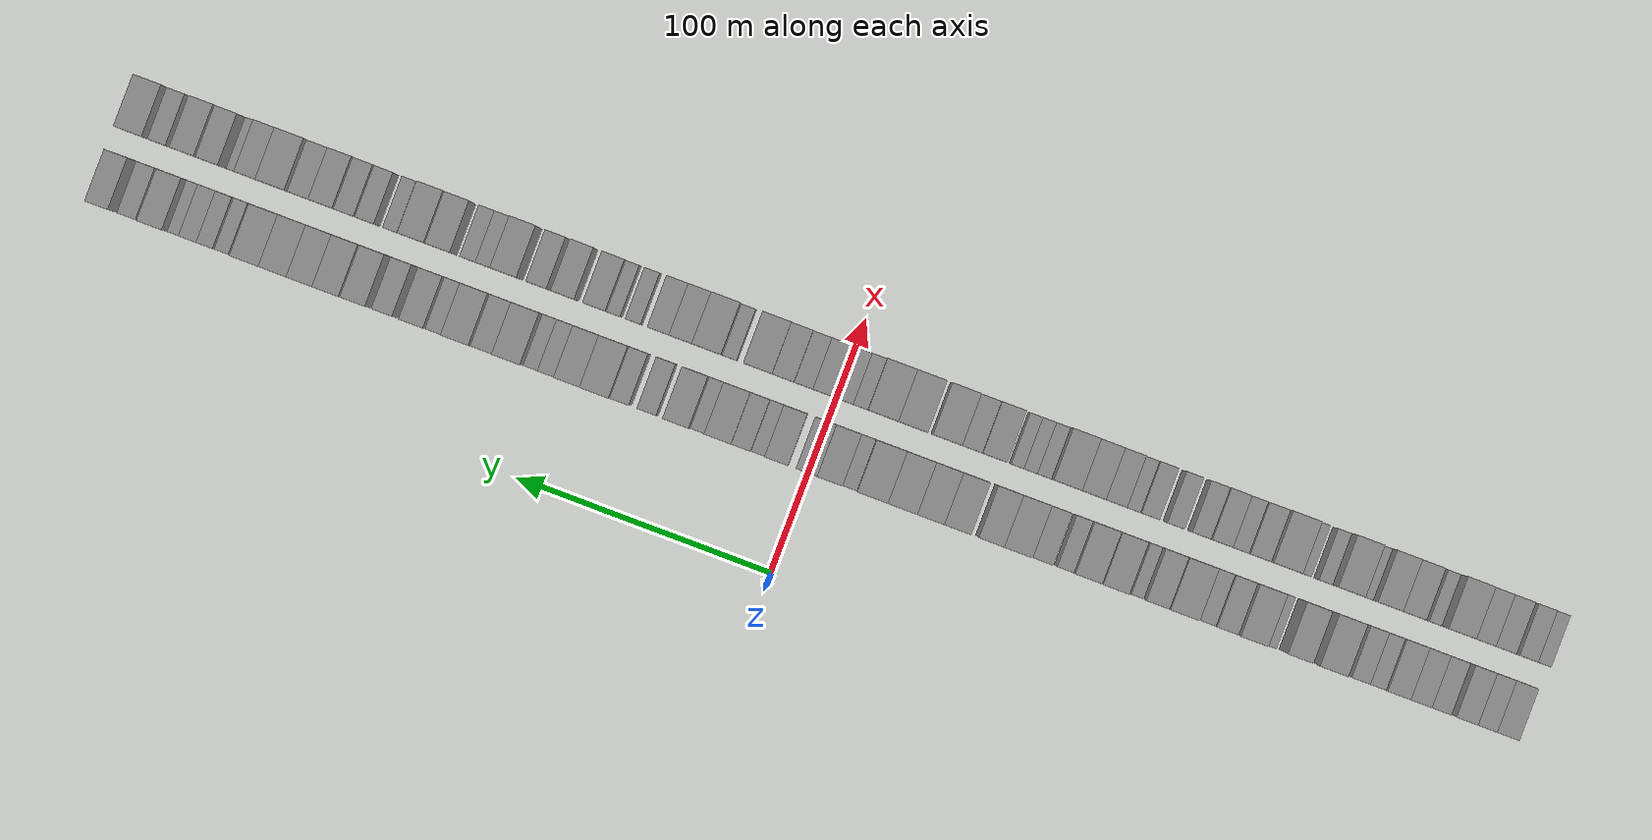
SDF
<sdf version="1.6">
 <world name="default">
  <scene>
   <sky><clouds><speed>12</speed></clouds></sky>
   <ambient>0.4 0.4 0.4 1</ambient>
   <background>0.7 0.7 0.7 1</background>
   <shadows>1</shadows>
  </scene>
  <gravity>0 0 -9.8066</gravity>
  <magnetic_field>6e-06 2.3e-05 -4.2e-05</magnetic_field>
  <physics default="0" name="default_physics" type="ode">
   <ode>
    <solver>
     <type>quick</type>
     <iters>10</iters>
     <sor>1.0</sor>
     <use_dynamic_moi_rescaling>0</use_dynamic_moi_rescaling>
    </solver>
    <constraints>
     <cfm>0</cfm>
     <erp>0.2</erp>
     <contact_max_correcting_vel>100</contact_max_correcting_vel>
     <contact_surface_layer>0.001</contact_surface_layer>
    </constraints>
   </ode>
   <max_step_size>0.004</max_step_size>
   <real_time_factor>1</real_time_factor>
   <real_time_update_rate>250</real_time_update_rate>
  </physics>
  <light name="sun" type="directional">
   <pose>0 0 10 0 0 0</pose>
   <diffuse>0.8 0.8 0.8 1</diffuse>
   <specular>0.2 0.2 0.2 1</specular>
   <attenuation>
    <range>1000</range>
    <constant>0.9</constant>
    <linear>0.01</linear>
    <quadratic>0.001</quadratic>
   </attenuation>
   <direction>-0.5 0.1 -0.9</direction>
  </light>
  <model name="building_1">
   <static>1</static>
   <pose>50.0000 -270.7168 0 0.000000 0.000000 0.000000</pose>
   <link name="link">
    <pose>0 0 9.00 0 0 0</pose>
    <collision name="collision"><geometry><box><size>20.0000 8.5664 18.0000</size></box></geometry></collision>
    <visual name="visual">
     <cast_shadows>0</cast_shadows>
     <geometry><box><size>20.0000 8.5664 18.0000</size></box></geometry>
     <material>
      <script>
       <uri>model://grey_wall/materials/scripts</uri>
       <uri>model://grey_wall/materials/textures</uri>
       <name>vrc/grey_wall</name>
      </script>
     </material>
    </visual>
   </link>
  </model>
  <model name="building_2">
   <static>1</static>
   <pose>50.0000 -262.7219 0 0.000000 0.000000 0.000000</pose>
   <link name="link">
    <pose>0 0 9.00 0 0 0</pose>
    <collision name="collision"><geometry><box><size>20.0000 7.4233 18.0000</size></box></geometry></collision>
    <visual name="visual">
     <cast_shadows>0</cast_shadows>
     <geometry><box><size>20.0000 7.4233 18.0000</size></box></geometry>
     <material>
      <script>
       <uri>model://grey_wall/materials/scripts</uri>
       <uri>model://grey_wall/materials/textures</uri>
       <name>vrc/grey_wall</name>
      </script>
     </material>
    </visual>
   </link>
  </model>
  <model name="building_3">
   <static>1</static>
   <pose>50.0000 -254.8419 0 0.000000 0.000000 0.000000</pose>
   <link name="link">
    <pose>0 0 9.00 0 0 0</pose>
    <collision name="collision"><geometry><box><size>20.0000 8.3367 18.0000</size></box></geometry></collision>
    <visual name="visual">
     <cast_shadows>0</cast_shadows>
     <geometry><box><size>20.0000 8.3367 18.0000</size></box></geometry>
     <material>
      <script>
       <uri>model://grey_wall/materials/scripts</uri>
       <uri>model://grey_wall/materials/textures</uri>
       <name>vrc/grey_wall</name>
      </script>
     </material>
    </visual>
   </link>
  </model>
  <model name="building_4">
   <static>1</static>
   <pose>50.0000 -244.9049 0 0.000000 0.000000 0.000000</pose>
   <link name="link">
    <pose>0 0 9.00 0 0 0</pose>
    <collision name="collision"><geometry><box><size>20.0000 7.5373 18.0000</size></box></geometry></collision>
    <visual name="visual">
     <cast_shadows>0</cast_shadows>
     <geometry><box><size>20.0000 7.5373 18.0000</size></box></geometry>
     <material>
      <script>
       <uri>model://grey_wall/materials/scripts</uri>
       <uri>model://grey_wall/materials/textures</uri>
       <name>vrc/grey_wall</name>
      </script>
     </material>
    </visual>
   </link>
  </model>
  <model name="building_5">
   <static>1</static>
   <pose>50.0000 -237.0605 0 0.000000 0.000000 0.000000</pose>
   <link name="link">
    <pose>0 0 9.00 0 0 0</pose>
    <collision name="collision"><geometry><box><size>20.0000 8.1513 18.0000</size></box></geometry></collision>
    <visual name="visual">
     <cast_shadows>0</cast_shadows>
     <geometry><box><size>20.0000 8.1513 18.0000</size></box></geometry>
     <material>
      <script>
       <uri>model://grey_wall/materials/scripts</uri>
       <uri>model://grey_wall/materials/textures</uri>
       <name>vrc/grey_wall</name>
      </script>
     </material>
    </visual>
   </link>
  </model>
  <model name="building_6">
   <static>1</static>
   <pose>50.0000 -228.5198 0 0.000000 0.000000 0.000000</pose>
   <link name="link">
    <pose>0 0 9.00 0 0 0</pose>
    <collision name="collision"><geometry><box><size>20.0000 8.9301 18.0000</size></box></geometry></collision>
    <visual name="visual">
     <cast_shadows>0</cast_shadows>
     <geometry><box><size>20.0000 8.9301 18.0000</size></box></geometry>
     <material>
      <script>
       <uri>model://grey_wall/materials/scripts</uri>
       <uri>model://grey_wall/materials/textures</uri>
       <name>vrc/grey_wall</name>
      </script>
     </material>
    </visual>
   </link>
  </model>
  <model name="building_7">
   <static>1</static>
   <pose>50.0000 -220.9918 0 0.000000 0.000000 0.000000</pose>
   <link name="link">
    <pose>0 0 7.50 0 0 0</pose>
    <collision name="collision"><geometry><box><size>20.0000 6.1259 15.0000</size></box></geometry></collision>
    <visual name="visual">
     <cast_shadows>0</cast_shadows>
     <geometry><box><size>20.0000 6.1259 15.0000</size></box></geometry>
     <material>
      <script>
       <uri>model://grey_wall/materials/scripts</uri>
       <uri>model://grey_wall/materials/textures</uri>
       <name>vrc/grey_wall</name>
      </script>
     </material>
    </visual>
   </link>
  </model>
  <model name="building_8">
   <static>1</static>
   <pose>50.0000 -214.3216 0 0.000000 0.000000 0.000000</pose>
   <link name="link">
    <pose>0 0 7.50 0 0 0</pose>
    <collision name="collision"><geometry><box><size>20.0000 7.2145 15.0000</size></box></geometry></collision>
    <visual name="visual">
     <cast_shadows>0</cast_shadows>
     <geometry><box><size>20.0000 7.2145 15.0000</size></box></geometry>
     <material>
      <script>
       <uri>model://grey_wall/materials/scripts</uri>
       <uri>model://grey_wall/materials/textures</uri>
       <name>vrc/grey_wall</name>
      </script>
     </material>
    </visual>
   </link>
  </model>
  <model name="building_9">
   <static>1</static>
   <pose>50.0000 -202.2630 0 0.000000 0.000000 0.000000</pose>
   <link name="link">
    <pose>0 0 12.00 0 0 0</pose>
    <collision name="collision"><geometry><box><size>20.0000 10.9027 24.0000</size></box></geometry></collision>
    <visual name="visual">
     <cast_shadows>0</cast_shadows>
     <geometry><box><size>20.0000 10.9027 24.0000</size></box></geometry>
     <material>
      <script>
       <uri>model://grey_wall/materials/scripts</uri>
       <uri>model://grey_wall/materials/textures</uri>
       <name>vrc/grey_wall</name>
      </script>
     </material>
    </visual>
   </link>
  </model>
  <model name="building_10">
   <static>1</static>
   <pose>50.0000 -189.8915 0 0.000000 0.000000 0.000000</pose>
   <link name="link">
    <pose>0 0 10.50 0 0 0</pose>
    <collision name="collision"><geometry><box><size>20.0000 9.8403 21.0000</size></box></geometry></collision>
    <visual name="visual">
     <cast_shadows>0</cast_shadows>
     <geometry><box><size>20.0000 9.8403 21.0000</size></box></geometry>
     <material>
      <script>
       <uri>model://grey_wall/materials/scripts</uri>
       <uri>model://grey_wall/materials/textures</uri>
       <name>vrc/grey_wall</name>
      </script>
     </material>
    </visual>
   </link>
  </model>
  <model name="building_11">
   <static>1</static>
   <pose>50.0000 -179.4758 0 0.000000 0.000000 0.000000</pose>
   <link name="link">
    <pose>0 0 6.00 0 0 0</pose>
    <collision name="collision"><geometry><box><size>20.0000 4.9911 12.0000</size></box></geometry></collision>
    <visual name="visual">
     <cast_shadows>0</cast_shadows>
     <geometry><box><size>20.0000 4.9911 12.0000</size></box></geometry>
     <material>
      <script>
       <uri>model://grey_wall/materials/scripts</uri>
       <uri>model://grey_wall/materials/textures</uri>
       <name>vrc/grey_wall</name>
      </script>
     </material>
    </visual>
   </link>
  </model>
  <model name="building_12">
   <static>1</static>
   <pose>50.0000 -171.6714 0 0.000000 0.000000 0.000000</pose>
   <link name="link">
    <pose>0 0 12.00 0 0 0</pose>
    <collision name="collision"><geometry><box><size>20.0000 10.6177 24.0000</size></box></geometry></collision>
    <visual name="visual">
     <cast_shadows>0</cast_shadows>
     <geometry><box><size>20.0000 10.6177 24.0000</size></box></geometry>
     <material>
      <script>
       <uri>model://grey_wall/materials/scripts</uri>
       <uri>model://grey_wall/materials/textures</uri>
       <name>vrc/grey_wall</name>
      </script>
     </material>
    </visual>
   </link>
  </model>
  <model name="building_13">
   <static>1</static>
   <pose>50.0000 -162.2063 0 0.000000 0.000000 0.000000</pose>
   <link name="link">
    <pose>0 0 9.00 0 0 0</pose>
    <collision name="collision"><geometry><box><size>20.0000 8.3125 18.0000</size></box></geometry></collision>
    <visual name="visual">
     <cast_shadows>0</cast_shadows>
     <geometry><box><size>20.0000 8.3125 18.0000</size></box></geometry>
     <material>
      <script>
       <uri>model://grey_wall/materials/scripts</uri>
       <uri>model://grey_wall/materials/textures</uri>
       <name>vrc/grey_wall</name>
      </script>
     </material>
    </visual>
   </link>
  </model>
  <model name="building_14">
   <static>1</static>
   <pose>50.0000 -154.3164 0 0.000000 0.000000 0.000000</pose>
   <link name="link">
    <pose>0 0 7.50 0 0 0</pose>
    <collision name="collision"><geometry><box><size>20.0000 7.4673 15.0000</size></box></geometry></collision>
    <visual name="visual">
     <cast_shadows>0</cast_shadows>
     <geometry><box><size>20.0000 7.4673 15.0000</size></box></geometry>
     <material>
      <script>
       <uri>model://grey_wall/materials/scripts</uri>
       <uri>model://grey_wall/materials/textures</uri>
       <name>vrc/grey_wall</name>
      </script>
     </material>
    </visual>
   </link>
  </model>
  <model name="building_15">
   <static>1</static>
   <pose>50.0000 -144.9487 0 0.000000 0.000000 0.000000</pose>
   <link name="link">
    <pose>0 0 12.00 0 0 0</pose>
    <collision name="collision"><geometry><box><size>20.0000 11.2681 24.0000</size></box></geometry></collision>
    <visual name="visual">
     <cast_shadows>0</cast_shadows>
     <geometry><box><size>20.0000 11.2681 24.0000</size></box></geometry>
     <material>
      <script>
       <uri>model://grey_wall/materials/scripts</uri>
       <uri>model://grey_wall/materials/textures</uri>
       <name>vrc/grey_wall</name>
      </script>
     </material>
    </visual>
   </link>
  </model>
  <model name="building_16">
   <static>1</static>
   <pose>50.0000 -134.8503 0 0.000000 0.000000 0.000000</pose>
   <link name="link">
    <pose>0 0 10.50 0 0 0</pose>
    <collision name="collision"><geometry><box><size>20.0000 8.9286 21.0000</size></box></geometry></collision>
    <visual name="visual">
     <cast_shadows>0</cast_shadows>
     <geometry><box><size>20.0000 8.9286 21.0000</size></box></geometry>
     <material>
      <script>
       <uri>model://grey_wall/materials/scripts</uri>
       <uri>model://grey_wall/materials/textures</uri>
       <name>vrc/grey_wall</name>
      </script>
     </material>
    </visual>
   </link>
  </model>
  <model name="building_17">
   <static>1</static>
   <pose>50.0000 -127.9544 0 0.000000 0.000000 0.000000</pose>
   <link name="link">
    <pose>0 0 6.00 0 0 0</pose>
    <collision name="collision"><geometry><box><size>20.0000 4.8633 12.0000</size></box></geometry></collision>
    <visual name="visual">
     <cast_shadows>0</cast_shadows>
     <geometry><box><size>20.0000 4.8633 12.0000</size></box></geometry>
     <material>
      <script>
       <uri>model://grey_wall/materials/scripts</uri>
       <uri>model://grey_wall/materials/textures</uri>
       <name>vrc/grey_wall</name>
      </script>
     </material>
    </visual>
   </link>
  </model>
  <model name="building_18">
   <static>1</static>
   <pose>50.0000 -118.4666 0 0.000000 0.000000 0.000000</pose>
   <link name="link">
    <pose>0 0 12.00 0 0 0</pose>
    <collision name="collision"><geometry><box><size>20.0000 10.1121 24.0000</size></box></geometry></collision>
    <visual name="visual">
     <cast_shadows>0</cast_shadows>
     <geometry><box><size>20.0000 10.1121 24.0000</size></box></geometry>
     <material>
      <script>
       <uri>model://grey_wall/materials/scripts</uri>
       <uri>model://grey_wall/materials/textures</uri>
       <name>vrc/grey_wall</name>
      </script>
     </material>
    </visual>
   </link>
  </model>
  <model name="building_19">
   <static>1</static>
   <pose>50.0000 -108.1889 0 0.000000 0.000000 0.000000</pose>
   <link name="link">
    <pose>0 0 10.50 0 0 0</pose>
    <collision name="collision"><geometry><box><size>20.0000 10.4434 21.0000</size></box></geometry></collision>
    <visual name="visual">
     <cast_shadows>0</cast_shadows>
     <geometry><box><size>20.0000 10.4434 21.0000</size></box></geometry>
     <material>
      <script>
       <uri>model://grey_wall/materials/scripts</uri>
       <uri>model://grey_wall/materials/textures</uri>
       <name>vrc/grey_wall</name>
      </script>
     </material>
    </visual>
   </link>
  </model>
  <model name="building_20">
   <static>1</static>
   <pose>50.0000 -99.7543 0 0.000000 0.000000 0.000000</pose>
   <link name="link">
    <pose>0 0 7.50 0 0 0</pose>
    <collision name="collision"><geometry><box><size>20.0000 6.4258 15.0000</size></box></geometry></collision>
    <visual name="visual">
     <cast_shadows>0</cast_shadows>
     <geometry><box><size>20.0000 6.4258 15.0000</size></box></geometry>
     <material>
      <script>
       <uri>model://grey_wall/materials/scripts</uri>
       <uri>model://grey_wall/materials/textures</uri>
       <name>vrc/grey_wall</name>
      </script>
     </material>
    </visual>
   </link>
  </model>
  <model name="building_21">
   <static>1</static>
   <pose>50.0000 -90.4187 0 0.000000 0.000000 0.000000</pose>
   <link name="link">
    <pose>0 0 9.00 0 0 0</pose>
    <collision name="collision"><geometry><box><size>20.0000 8.2455 18.0000</size></box></geometry></collision>
    <visual name="visual">
     <cast_shadows>0</cast_shadows>
     <geometry><box><size>20.0000 8.2455 18.0000</size></box></geometry>
     <material>
      <script>
       <uri>model://grey_wall/materials/scripts</uri>
       <uri>model://grey_wall/materials/textures</uri>
       <name>vrc/grey_wall</name>
      </script>
     </material>
    </visual>
   </link>
  </model>
  <model name="building_22">
   <static>1</static>
   <pose>50.0000 -80.8268 0 0.000000 0.000000 0.000000</pose>
   <link name="link">
    <pose>0 0 12.00 0 0 0</pose>
    <collision name="collision"><geometry><box><size>20.0000 10.9381 24.0000</size></box></geometry></collision>
    <visual name="visual">
     <cast_shadows>0</cast_shadows>
     <geometry><box><size>20.0000 10.9381 24.0000</size></box></geometry>
     <material>
      <script>
       <uri>model://grey_wall/materials/scripts</uri>
       <uri>model://grey_wall/materials/textures</uri>
       <name>vrc/grey_wall</name>
      </script>
     </material>
    </visual>
   </link>
  </model>
  <model name="building_23">
   <static>1</static>
   <pose>50.0000 -70.4819 0 0.000000 0.000000 0.000000</pose>
   <link name="link">
    <pose>0 0 12.00 0 0 0</pose>
    <collision name="collision"><geometry><box><size>20.0000 9.7517 24.0000</size></box></geometry></collision>
    <visual name="visual">
     <cast_shadows>0</cast_shadows>
     <geometry><box><size>20.0000 9.7517 24.0000</size></box></geometry>
     <material>
      <script>
       <uri>model://grey_wall/materials/scripts</uri>
       <uri>model://grey_wall/materials/textures</uri>
       <name>vrc/grey_wall</name>
      </script>
     </material>
    </visual>
   </link>
  </model>
  <model name="building_24">
   <static>1</static>
   <pose>50.0000 -57.4572 0 0.000000 0.000000 0.000000</pose>
   <link name="link">
    <pose>0 0 12.00 0 0 0</pose>
    <collision name="collision"><geometry><box><size>20.0000 10.2979 24.0000</size></box></geometry></collision>
    <visual name="visual">
     <cast_shadows>0</cast_shadows>
     <geometry><box><size>20.0000 10.2979 24.0000</size></box></geometry>
     <material>
      <script>
       <uri>model://grey_wall/materials/scripts</uri>
       <uri>model://grey_wall/materials/textures</uri>
       <name>vrc/grey_wall</name>
      </script>
     </material>
    </visual>
   </link>
  </model>
  <model name="building_25">
   <static>1</static>
   <pose>50.0000 -47.1067 0 0.000000 0.000000 0.000000</pose>
   <link name="link">
    <pose>0 0 12.00 0 0 0</pose>
    <collision name="collision"><geometry><box><size>20.0000 10.4030 24.0000</size></box></geometry></collision>
    <visual name="visual">
     <cast_shadows>0</cast_shadows>
     <geometry><box><size>20.0000 10.4030 24.0000</size></box></geometry>
     <material>
      <script>
       <uri>model://grey_wall/materials/scripts</uri>
       <uri>model://grey_wall/materials/textures</uri>
       <name>vrc/grey_wall</name>
      </script>
     </material>
    </visual>
   </link>
  </model>
  <model name="building_26">
   <static>1</static>
   <pose>50.0000 -36.2459 0 0.000000 0.000000 0.000000</pose>
   <link name="link">
    <pose>0 0 12.00 0 0 0</pose>
    <collision name="collision"><geometry><box><size>20.0000 11.3186 24.0000</size></box></geometry></collision>
    <visual name="visual">
     <cast_shadows>0</cast_shadows>
     <geometry><box><size>20.0000 11.3186 24.0000</size></box></geometry>
     <material>
      <script>
       <uri>model://grey_wall/materials/scripts</uri>
       <uri>model://grey_wall/materials/textures</uri>
       <name>vrc/grey_wall</name>
      </script>
     </material>
    </visual>
   </link>
  </model>
  <model name="building_27">
   <static>1</static>
   <pose>50.0000 -24.6920 0 0.000000 0.000000 0.000000</pose>
   <link name="link">
    <pose>0 0 12.00 0 0 0</pose>
    <collision name="collision"><geometry><box><size>20.0000 11.7893 24.0000</size></box></geometry></collision>
    <visual name="visual">
     <cast_shadows>0</cast_shadows>
     <geometry><box><size>20.0000 11.7893 24.0000</size></box></geometry>
     <material>
      <script>
       <uri>model://grey_wall/materials/scripts</uri>
       <uri>model://grey_wall/materials/textures</uri>
       <name>vrc/grey_wall</name>
      </script>
     </material>
    </visual>
   </link>
  </model>
  <model name="building_28">
   <static>1</static>
   <pose>50.0000 -15.9460 0 0.000000 0.000000 0.000000</pose>
   <link name="link">
    <pose>0 0 6.00 0 0 0</pose>
    <collision name="collision"><geometry><box><size>20.0000 5.7028 12.0000</size></box></geometry></collision>
    <visual name="visual">
     <cast_shadows>0</cast_shadows>
     <geometry><box><size>20.0000 5.7028 12.0000</size></box></geometry>
     <material>
      <script>
       <uri>model://grey_wall/materials/scripts</uri>
       <uri>model://grey_wall/materials/textures</uri>
       <name>vrc/grey_wall</name>
      </script>
     </material>
    </visual>
   </link>
  </model>
  <model name="building_29">
   <static>1</static>
   <pose>50.0000 -8.2112 0 0.000000 0.000000 0.000000</pose>
   <link name="link">
    <pose>0 0 10.50 0 0 0</pose>
    <collision name="collision"><geometry><box><size>20.0000 9.7667 21.0000</size></box></geometry></collision>
    <visual name="visual">
     <cast_shadows>0</cast_shadows>
     <geometry><box><size>20.0000 9.7667 21.0000</size></box></geometry>
     <material>
      <script>
       <uri>model://grey_wall/materials/scripts</uri>
       <uri>model://grey_wall/materials/textures</uri>
       <name>vrc/grey_wall</name>
      </script>
     </material>
    </visual>
   </link>
  </model>
  <model name="building_30">
   <static>1</static>
   <pose>50.0000 0.7794 0 0.000000 0.000000 0.000000</pose>
   <link name="link">
    <pose>0 0 9.00 0 0 0</pose>
    <collision name="collision"><geometry><box><size>20.0000 8.2147 18.0000</size></box></geometry></collision>
    <visual name="visual">
     <cast_shadows>0</cast_shadows>
     <geometry><box><size>20.0000 8.2147 18.0000</size></box></geometry>
     <material>
      <script>
       <uri>model://grey_wall/materials/scripts</uri>
       <uri>model://grey_wall/materials/textures</uri>
       <name>vrc/grey_wall</name>
      </script>
     </material>
    </visual>
   </link>
  </model>
  <model name="building_31">
   <static>1</static>
   <pose>50.0000 12.4411 0 0.000000 0.000000 0.000000</pose>
   <link name="link">
    <pose>0 0 10.50 0 0 0</pose>
    <collision name="collision"><geometry><box><size>20.0000 9.1086 21.0000</size></box></geometry></collision>
    <visual name="visual">
     <cast_shadows>0</cast_shadows>
     <geometry><box><size>20.0000 9.1086 21.0000</size></box></geometry>
     <material>
      <script>
       <uri>model://grey_wall/materials/scripts</uri>
       <uri>model://grey_wall/materials/textures</uri>
       <name>vrc/grey_wall</name>
      </script>
     </material>
    </visual>
   </link>
  </model>
  <model name="building_32">
   <static>1</static>
   <pose>50.0000 19.7043 0 0.000000 0.000000 0.000000</pose>
   <link name="link">
    <pose>0 0 6.00 0 0 0</pose>
    <collision name="collision"><geometry><box><size>20.0000 5.4179 12.0000</size></box></geometry></collision>
    <visual name="visual">
     <cast_shadows>0</cast_shadows>
     <geometry><box><size>20.0000 5.4179 12.0000</size></box></geometry>
     <material>
      <script>
       <uri>model://grey_wall/materials/scripts</uri>
       <uri>model://grey_wall/materials/textures</uri>
       <name>vrc/grey_wall</name>
      </script>
     </material>
    </visual>
   </link>
  </model>
  <model name="building_33">
   <static>1</static>
   <pose>50.0000 26.1778 0 0.000000 0.000000 0.000000</pose>
   <link name="link">
    <pose>0 0 9.00 0 0 0</pose>
    <collision name="collision"><geometry><box><size>20.0000 7.5290 18.0000</size></box></geometry></collision>
    <visual name="visual">
     <cast_shadows>0</cast_shadows>
     <geometry><box><size>20.0000 7.5290 18.0000</size></box></geometry>
     <material>
      <script>
       <uri>model://grey_wall/materials/scripts</uri>
       <uri>model://grey_wall/materials/textures</uri>
       <name>vrc/grey_wall</name>
      </script>
     </material>
    </visual>
   </link>
  </model>
  <model name="building_34">
   <static>1</static>
   <pose>50.0000 35.1295 0 0.000000 0.000000 0.000000</pose>
   <link name="link">
    <pose>0 0 10.50 0 0 0</pose>
    <collision name="collision"><geometry><box><size>20.0000 10.3746 21.0000</size></box></geometry></collision>
    <visual name="visual">
     <cast_shadows>0</cast_shadows>
     <geometry><box><size>20.0000 10.3746 21.0000</size></box></geometry>
     <material>
      <script>
       <uri>model://grey_wall/materials/scripts</uri>
       <uri>model://grey_wall/materials/textures</uri>
       <name>vrc/grey_wall</name>
      </script>
     </material>
    </visual>
   </link>
  </model>
  <model name="building_35">
   <static>1</static>
   <pose>50.0000 43.2426 0 0.000000 0.000000 0.000000</pose>
   <link name="link">
    <pose>0 0 6.00 0 0 0</pose>
    <collision name="collision"><geometry><box><size>20.0000 5.8516 12.0000</size></box></geometry></collision>
    <visual name="visual">
     <cast_shadows>0</cast_shadows>
     <geometry><box><size>20.0000 5.8516 12.0000</size></box></geometry>
     <material>
      <script>
       <uri>model://grey_wall/materials/scripts</uri>
       <uri>model://grey_wall/materials/textures</uri>
       <name>vrc/grey_wall</name>
      </script>
     </material>
    </visual>
   </link>
  </model>
  <model name="building_36">
   <static>1</static>
   <pose>50.0000 51.1862 0 0.000000 0.000000 0.000000</pose>
   <link name="link">
    <pose>0 0 12.00 0 0 0</pose>
    <collision name="collision"><geometry><box><size>20.0000 10.0354 24.0000</size></box></geometry></collision>
    <visual name="visual">
     <cast_shadows>0</cast_shadows>
     <geometry><box><size>20.0000 10.0354 24.0000</size></box></geometry>
     <material>
      <script>
       <uri>model://grey_wall/materials/scripts</uri>
       <uri>model://grey_wall/materials/textures</uri>
       <name>vrc/grey_wall</name>
      </script>
     </material>
    </visual>
   </link>
  </model>
  <model name="building_37">
   <static>1</static>
   <pose>50.0000 62.9248 0 0.000000 0.000000 0.000000</pose>
   <link name="link">
    <pose>0 0 7.50 0 0 0</pose>
    <collision name="collision"><geometry><box><size>20.0000 7.4419 15.0000</size></box></geometry></collision>
    <visual name="visual">
     <cast_shadows>0</cast_shadows>
     <geometry><box><size>20.0000 7.4419 15.0000</size></box></geometry>
     <material>
      <script>
       <uri>model://grey_wall/materials/scripts</uri>
       <uri>model://grey_wall/materials/textures</uri>
       <name>vrc/grey_wall</name>
      </script>
     </material>
    </visual>
   </link>
  </model>
  <model name="building_38">
   <static>1</static>
   <pose>50.0000 73.3341 0 0.000000 0.000000 0.000000</pose>
   <link name="link">
    <pose>0 0 9.00 0 0 0</pose>
    <collision name="collision"><geometry><box><size>20.0000 7.3767 18.0000</size></box></geometry></collision>
    <visual name="visual">
     <cast_shadows>0</cast_shadows>
     <geometry><box><size>20.0000 7.3767 18.0000</size></box></geometry>
     <material>
      <script>
       <uri>model://grey_wall/materials/scripts</uri>
       <uri>model://grey_wall/materials/textures</uri>
       <name>vrc/grey_wall</name>
      </script>
     </material>
    </visual>
   </link>
  </model>
  <model name="building_39">
   <static>1</static>
   <pose>50.0000 82.6003 0 0.000000 0.000000 0.000000</pose>
   <link name="link">
    <pose>0 0 12.00 0 0 0</pose>
    <collision name="collision"><geometry><box><size>20.0000 11.1556 24.0000</size></box></geometry></collision>
    <visual name="visual">
     <cast_shadows>0</cast_shadows>
     <geometry><box><size>20.0000 11.1556 24.0000</size></box></geometry>
     <material>
      <script>
       <uri>model://grey_wall/materials/scripts</uri>
       <uri>model://grey_wall/materials/textures</uri>
       <name>vrc/grey_wall</name>
      </script>
     </material>
    </visual>
   </link>
  </model>
  <model name="building_40">
   <static>1</static>
   <pose>50.0000 93.3117 0 0.000000 0.000000 0.000000</pose>
   <link name="link">
    <pose>0 0 10.50 0 0 0</pose>
    <collision name="collision"><geometry><box><size>20.0000 10.2672 21.0000</size></box></geometry></collision>
    <visual name="visual">
     <cast_shadows>0</cast_shadows>
     <geometry><box><size>20.0000 10.2672 21.0000</size></box></geometry>
     <material>
      <script>
       <uri>model://grey_wall/materials/scripts</uri>
       <uri>model://grey_wall/materials/textures</uri>
       <name>vrc/grey_wall</name>
      </script>
     </material>
    </visual>
   </link>
  </model>
  <model name="building_41">
   <static>1</static>
   <pose>50.0000 101.8601 0 0.000000 0.000000 0.000000</pose>
   <link name="link">
    <pose>0 0 7.50 0 0 0</pose>
    <collision name="collision"><geometry><box><size>20.0000 6.8297 15.0000</size></box></geometry></collision>
    <visual name="visual">
     <cast_shadows>0</cast_shadows>
     <geometry><box><size>20.0000 6.8297 15.0000</size></box></geometry>
     <material>
      <script>
       <uri>model://grey_wall/materials/scripts</uri>
       <uri>model://grey_wall/materials/textures</uri>
       <name>vrc/grey_wall</name>
      </script>
     </material>
    </visual>
   </link>
  </model>
  <model name="building_42">
   <static>1</static>
   <pose>50.0000 108.1862 0 0.000000 0.000000 0.000000</pose>
   <link name="link">
    <pose>0 0 6.00 0 0 0</pose>
    <collision name="collision"><geometry><box><size>20.0000 5.8223 12.0000</size></box></geometry></collision>
    <visual name="visual">
     <cast_shadows>0</cast_shadows>
     <geometry><box><size>20.0000 5.8223 12.0000</size></box></geometry>
     <material>
      <script>
       <uri>model://grey_wall/materials/scripts</uri>
       <uri>model://grey_wall/materials/textures</uri>
       <name>vrc/grey_wall</name>
      </script>
     </material>
    </visual>
   </link>
  </model>
  <model name="building_43">
   <static>1</static>
   <pose>50.0000 116.5472 0 0.000000 0.000000 0.000000</pose>
   <link name="link">
    <pose>0 0 12.00 0 0 0</pose>
    <collision name="collision"><geometry><box><size>20.0000 10.8998 24.0000</size></box></geometry></collision>
    <visual name="visual">
     <cast_shadows>0</cast_shadows>
     <geometry><box><size>20.0000 10.8998 24.0000</size></box></geometry>
     <material>
      <script>
       <uri>model://grey_wall/materials/scripts</uri>
       <uri>model://grey_wall/materials/textures</uri>
       <name>vrc/grey_wall</name>
      </script>
     </material>
    </visual>
   </link>
  </model>
  <model name="building_44">
   <static>1</static>
   <pose>50.0000 126.4586 0 0.000000 0.000000 0.000000</pose>
   <link name="link">
    <pose>0 0 9.00 0 0 0</pose>
    <collision name="collision"><geometry><box><size>20.0000 8.9230 18.0000</size></box></geometry></collision>
    <visual name="visual">
     <cast_shadows>0</cast_shadows>
     <geometry><box><size>20.0000 8.9230 18.0000</size></box></geometry>
     <material>
      <script>
       <uri>model://grey_wall/materials/scripts</uri>
       <uri>model://grey_wall/materials/textures</uri>
       <name>vrc/grey_wall</name>
      </script>
     </material>
    </visual>
   </link>
  </model>
  <model name="building_45">
   <static>1</static>
   <pose>50.0000 136.2764 0 0.000000 0.000000 0.000000</pose>
   <link name="link">
    <pose>0 0 12.00 0 0 0</pose>
    <collision name="collision"><geometry><box><size>20.0000 10.7124 24.0000</size></box></geometry></collision>
    <visual name="visual">
     <cast_shadows>0</cast_shadows>
     <geometry><box><size>20.0000 10.7124 24.0000</size></box></geometry>
     <material>
      <script>
       <uri>model://grey_wall/materials/scripts</uri>
       <uri>model://grey_wall/materials/textures</uri>
       <name>vrc/grey_wall</name>
      </script>
     </material>
    </visual>
   </link>
  </model>
  <model name="building_46">
   <static>1</static>
   <pose>50.0000 145.2257 0 0.000000 0.000000 0.000000</pose>
   <link name="link">
    <pose>0 0 7.50 0 0 0</pose>
    <collision name="collision"><geometry><box><size>20.0000 7.1862 15.0000</size></box></geometry></collision>
    <visual name="visual">
     <cast_shadows>0</cast_shadows>
     <geometry><box><size>20.0000 7.1862 15.0000</size></box></geometry>
     <material>
      <script>
       <uri>model://grey_wall/materials/scripts</uri>
       <uri>model://grey_wall/materials/textures</uri>
       <name>vrc/grey_wall</name>
      </script>
     </material>
    </visual>
   </link>
  </model>
  <model name="building_47">
   <static>1</static>
   <pose>50.0000 153.5088 0 0.000000 0.000000 0.000000</pose>
   <link name="link">
    <pose>0 0 10.50 0 0 0</pose>
    <collision name="collision"><geometry><box><size>20.0000 9.3801 21.0000</size></box></geometry></collision>
    <visual name="visual">
     <cast_shadows>0</cast_shadows>
     <geometry><box><size>20.0000 9.3801 21.0000</size></box></geometry>
     <material>
      <script>
       <uri>model://grey_wall/materials/scripts</uri>
       <uri>model://grey_wall/materials/textures</uri>
       <name>vrc/grey_wall</name>
      </script>
     </material>
    </visual>
   </link>
  </model>
  <model name="building_48">
   <static>1</static>
   <pose>50.0000 165.1900 0 0.000000 0.000000 0.000000</pose>
   <link name="link">
    <pose>0 0 9.00 0 0 0</pose>
    <collision name="collision"><geometry><box><size>20.0000 7.9823 18.0000</size></box></geometry></collision>
    <visual name="visual">
     <cast_shadows>0</cast_shadows>
     <geometry><box><size>20.0000 7.9823 18.0000</size></box></geometry>
     <material>
      <script>
       <uri>model://grey_wall/materials/scripts</uri>
       <uri>model://grey_wall/materials/textures</uri>
       <name>vrc/grey_wall</name>
      </script>
     </material>
    </visual>
   </link>
  </model>
  <model name="building_49">
   <static>1</static>
   <pose>50.0000 176.0217 0 0.000000 0.000000 0.000000</pose>
   <link name="link">
    <pose>0 0 10.50 0 0 0</pose>
    <collision name="collision"><geometry><box><size>20.0000 9.6810 21.0000</size></box></geometry></collision>
    <visual name="visual">
     <cast_shadows>0</cast_shadows>
     <geometry><box><size>20.0000 9.6810 21.0000</size></box></geometry>
     <material>
      <script>
       <uri>model://grey_wall/materials/scripts</uri>
       <uri>model://grey_wall/materials/textures</uri>
       <name>vrc/grey_wall</name>
      </script>
     </material>
    </visual>
   </link>
  </model>
  <model name="building_50">
   <static>1</static>
   <pose>50.0000 185.9524 0 0.000000 0.000000 0.000000</pose>
   <link name="link">
    <pose>0 0 12.00 0 0 0</pose>
    <collision name="collision"><geometry><box><size>20.0000 10.1804 24.0000</size></box></geometry></collision>
    <visual name="visual">
     <cast_shadows>0</cast_shadows>
     <geometry><box><size>20.0000 10.1804 24.0000</size></box></geometry>
     <material>
      <script>
       <uri>model://grey_wall/materials/scripts</uri>
       <uri>model://grey_wall/materials/textures</uri>
       <name>vrc/grey_wall</name>
      </script>
     </material>
    </visual>
   </link>
  </model>
  <model name="building_51">
   <static>1</static>
   <pose>50.0000 196.0034 0 0.000000 0.000000 0.000000</pose>
   <link name="link">
    <pose>0 0 12.00 0 0 0</pose>
    <collision name="collision"><geometry><box><size>20.0000 9.9217 24.0000</size></box></geometry></collision>
    <visual name="visual">
     <cast_shadows>0</cast_shadows>
     <geometry><box><size>20.0000 9.9217 24.0000</size></box></geometry>
     <material>
      <script>
       <uri>model://grey_wall/materials/scripts</uri>
       <uri>model://grey_wall/materials/textures</uri>
       <name>vrc/grey_wall</name>
      </script>
     </material>
    </visual>
   </link>
  </model>
  <model name="building_52">
   <static>1</static>
   <pose>50.0000 206.3297 0 0.000000 0.000000 0.000000</pose>
   <link name="link">
    <pose>0 0 12.00 0 0 0</pose>
    <collision name="collision"><geometry><box><size>20.0000 10.7308 24.0000</size></box></geometry></collision>
    <visual name="visual">
     <cast_shadows>0</cast_shadows>
     <geometry><box><size>20.0000 10.7308 24.0000</size></box></geometry>
     <material>
      <script>
       <uri>model://grey_wall/materials/scripts</uri>
       <uri>model://grey_wall/materials/textures</uri>
       <name>vrc/grey_wall</name>
      </script>
     </material>
    </visual>
   </link>
  </model>
  <model name="building_53">
   <static>1</static>
   <pose>50.0000 217.2352 0 0.000000 0.000000 0.000000</pose>
   <link name="link">
    <pose>0 0 12.00 0 0 0</pose>
    <collision name="collision"><geometry><box><size>20.0000 11.0803 24.0000</size></box></geometry></collision>
    <visual name="visual">
     <cast_shadows>0</cast_shadows>
     <geometry><box><size>20.0000 11.0803 24.0000</size></box></geometry>
     <material>
      <script>
       <uri>model://grey_wall/materials/scripts</uri>
       <uri>model://grey_wall/materials/textures</uri>
       <name>vrc/grey_wall</name>
      </script>
     </material>
    </visual>
   </link>
  </model>
  <model name="building_54">
   <static>1</static>
   <pose>50.0000 228.5376 0 0.000000 0.000000 0.000000</pose>
   <link name="link">
    <pose>0 0 6.00 0 0 0</pose>
    <collision name="collision"><geometry><box><size>20.0000 5.5244 12.0000</size></box></geometry></collision>
    <visual name="visual">
     <cast_shadows>0</cast_shadows>
     <geometry><box><size>20.0000 5.5244 12.0000</size></box></geometry>
     <material>
      <script>
       <uri>model://grey_wall/materials/scripts</uri>
       <uri>model://grey_wall/materials/textures</uri>
       <name>vrc/grey_wall</name>
      </script>
     </material>
    </visual>
   </link>
  </model>
  <model name="building_55">
   <static>1</static>
   <pose>50.0000 234.4831 0 0.000000 0.000000 0.000000</pose>
   <link name="link">
    <pose>0 0 7.50 0 0 0</pose>
    <collision name="collision"><geometry><box><size>20.0000 6.3667 15.0000</size></box></geometry></collision>
    <visual name="visual">
     <cast_shadows>0</cast_shadows>
     <geometry><box><size>20.0000 6.3667 15.0000</size></box></geometry>
     <material>
      <script>
       <uri>model://grey_wall/materials/scripts</uri>
       <uri>model://grey_wall/materials/textures</uri>
       <name>vrc/grey_wall</name>
      </script>
     </material>
    </visual>
   </link>
  </model>
  <model name="building_56">
   <static>1</static>
   <pose>50.0000 241.0856 0 0.000000 0.000000 0.000000</pose>
   <link name="link">
    <pose>0 0 7.50 0 0 0</pose>
    <collision name="collision"><geometry><box><size>20.0000 6.8383 15.0000</size></box></geometry></collision>
    <visual name="visual">
     <cast_shadows>0</cast_shadows>
     <geometry><box><size>20.0000 6.8383 15.0000</size></box></geometry>
     <material>
      <script>
       <uri>model://grey_wall/materials/scripts</uri>
       <uri>model://grey_wall/materials/textures</uri>
       <name>vrc/grey_wall</name>
      </script>
     </material>
    </visual>
   </link>
  </model>
  <model name="building_57">
   <static>1</static>
   <pose>50.0000 247.0287 0 0.000000 0.000000 0.000000</pose>
   <link name="link">
    <pose>0 0 6.00 0 0 0</pose>
    <collision name="collision"><geometry><box><size>20.0000 5.0480 12.0000</size></box></geometry></collision>
    <visual name="visual">
     <cast_shadows>0</cast_shadows>
     <geometry><box><size>20.0000 5.0480 12.0000</size></box></geometry>
     <material>
      <script>
       <uri>model://grey_wall/materials/scripts</uri>
       <uri>model://grey_wall/materials/textures</uri>
       <name>vrc/grey_wall</name>
      </script>
     </material>
    </visual>
   </link>
  </model>
  <model name="building_58">
   <static>1</static>
   <pose>50.0000 254.3807 0 0.000000 0.000000 0.000000</pose>
   <link name="link">
    <pose>0 0 10.50 0 0 0</pose>
    <collision name="collision"><geometry><box><size>20.0000 9.6561 21.0000</size></box></geometry></collision>
    <visual name="visual">
     <cast_shadows>0</cast_shadows>
     <geometry><box><size>20.0000 9.6561 21.0000</size></box></geometry>
     <material>
      <script>
       <uri>model://grey_wall/materials/scripts</uri>
       <uri>model://grey_wall/materials/textures</uri>
       <name>vrc/grey_wall</name>
      </script>
     </material>
    </visual>
   </link>
  </model>
  <model name="building_59">
   <static>1</static>
   <pose>50.0000 264.7727 0 0.000000 0.000000 0.000000</pose>
   <link name="link">
    <pose>0 0 7.50 0 0 0</pose>
    <collision name="collision"><geometry><box><size>20.0000 7.1280 15.0000</size></box></geometry></collision>
    <visual name="visual">
     <cast_shadows>0</cast_shadows>
     <geometry><box><size>20.0000 7.1280 15.0000</size></box></geometry>
     <material>
      <script>
       <uri>model://grey_wall/materials/scripts</uri>
       <uri>model://grey_wall/materials/textures</uri>
       <name>vrc/grey_wall</name>
      </script>
     </material>
    </visual>
   </link>
  </model>
  <model name="building_60">
   <static>1</static>
   <pose>50.0000 274.7963 0 0.000000 0.000000 0.000000</pose>
   <link name="link">
    <pose>0 0 10.50 0 0 0</pose>
    <collision name="collision"><geometry><box><size>20.0000 8.9191 21.0000</size></box></geometry></collision>
    <visual name="visual">
     <cast_shadows>0</cast_shadows>
     <geometry><box><size>20.0000 8.9191 21.0000</size></box></geometry>
     <material>
      <script>
       <uri>model://grey_wall/materials/scripts</uri>
       <uri>model://grey_wall/materials/textures</uri>
       <name>vrc/grey_wall</name>
      </script>
     </material>
    </visual>
   </link>
  </model>
  <model name="building_61">
   <static>1</static>
   <pose>79.0000 -275.0721 0 0.000000 0.000000 0.000000</pose>
   <link name="link">
    <pose>0 0 6.00 0 0 0</pose>
    <collision name="collision"><geometry><box><size>20.0000 5.8558 12.0000</size></box></geometry></collision>
    <visual name="visual">
     <cast_shadows>0</cast_shadows>
     <geometry><box><size>20.0000 5.8558 12.0000</size></box></geometry>
     <material>
      <script>
       <uri>model://grey_wall/materials/scripts</uri>
       <uri>model://grey_wall/materials/textures</uri>
       <name>vrc/grey_wall</name>
      </script>
     </material>
    </visual>
   </link>
  </model>
  <model name="building_62">
   <static>1</static>
   <pose>79.0000 -268.5609 0 0.000000 0.000000 0.000000</pose>
   <link name="link">
    <pose>0 0 7.50 0 0 0</pose>
    <collision name="collision"><geometry><box><size>20.0000 7.1666 15.0000</size></box></geometry></collision>
    <visual name="visual">
     <cast_shadows>0</cast_shadows>
     <geometry><box><size>20.0000 7.1666 15.0000</size></box></geometry>
     <material>
      <script>
       <uri>model://grey_wall/materials/scripts</uri>
       <uri>model://grey_wall/materials/textures</uri>
       <name>vrc/grey_wall</name>
      </script>
     </material>
    </visual>
   </link>
  </model>
  <model name="building_63">
   <static>1</static>
   <pose>79.0000 -258.9908 0 0.000000 0.000000 0.000000</pose>
   <link name="link">
    <pose>0 0 9.00 0 0 0</pose>
    <collision name="collision"><geometry><box><size>20.0000 7.9735 18.0000</size></box></geometry></collision>
    <visual name="visual">
     <cast_shadows>0</cast_shadows>
     <geometry><box><size>20.0000 7.9735 18.0000</size></box></geometry>
     <material>
      <script>
       <uri>model://grey_wall/materials/scripts</uri>
       <uri>model://grey_wall/materials/textures</uri>
       <name>vrc/grey_wall</name>
      </script>
     </material>
    </visual>
   </link>
  </model>
  <model name="building_64">
   <static>1</static>
   <pose>79.0000 -250.5445 0 0.000000 0.000000 0.000000</pose>
   <link name="link">
    <pose>0 0 9.00 0 0 0</pose>
    <collision name="collision"><geometry><box><size>20.0000 8.9191 18.0000</size></box></geometry></collision>
    <visual name="visual">
     <cast_shadows>0</cast_shadows>
     <geometry><box><size>20.0000 8.9191 18.0000</size></box></geometry>
     <material>
      <script>
       <uri>model://grey_wall/materials/scripts</uri>
       <uri>model://grey_wall/materials/textures</uri>
       <name>vrc/grey_wall</name>
      </script>
     </material>
    </visual>
   </link>
  </model>
  <model name="building_65">
   <static>1</static>
   <pose>79.0000 -240.7412 0 0.000000 0.000000 0.000000</pose>
   <link name="link">
    <pose>0 0 12.00 0 0 0</pose>
    <collision name="collision"><geometry><box><size>20.0000 10.6875 24.0000</size></box></geometry></collision>
    <visual name="visual">
     <cast_shadows>0</cast_shadows>
     <geometry><box><size>20.0000 10.6875 24.0000</size></box></geometry>
     <material>
      <script>
       <uri>model://grey_wall/materials/scripts</uri>
       <uri>model://grey_wall/materials/textures</uri>
       <name>vrc/grey_wall</name>
      </script>
     </material>
    </visual>
   </link>
  </model>
  <model name="building_66">
   <static>1</static>
   <pose>79.0000 -232.9635 0 0.000000 0.000000 0.000000</pose>
   <link name="link">
    <pose>0 0 6.00 0 0 0</pose>
    <collision name="collision"><geometry><box><size>20.0000 4.8679 12.0000</size></box></geometry></collision>
    <visual name="visual">
     <cast_shadows>0</cast_shadows>
     <geometry><box><size>20.0000 4.8679 12.0000</size></box></geometry>
     <material>
      <script>
       <uri>model://grey_wall/materials/scripts</uri>
       <uri>model://grey_wall/materials/textures</uri>
       <name>vrc/grey_wall</name>
      </script>
     </material>
    </visual>
   </link>
  </model>
  <model name="building_67">
   <static>1</static>
   <pose>79.0000 -223.0321 0 0.000000 0.000000 0.000000</pose>
   <link name="link">
    <pose>0 0 10.50 0 0 0</pose>
    <collision name="collision"><geometry><box><size>20.0000 8.9949 21.0000</size></box></geometry></collision>
    <visual name="visual">
     <cast_shadows>0</cast_shadows>
     <geometry><box><size>20.0000 8.9949 21.0000</size></box></geometry>
     <material>
      <script>
       <uri>model://grey_wall/materials/scripts</uri>
       <uri>model://grey_wall/materials/textures</uri>
       <name>vrc/grey_wall</name>
      </script>
     </material>
    </visual>
   </link>
  </model>
  <model name="building_68">
   <static>1</static>
   <pose>79.0000 -213.6621 0 0.000000 0.000000 0.000000</pose>
   <link name="link">
    <pose>0 0 10.50 0 0 0</pose>
    <collision name="collision"><geometry><box><size>20.0000 9.7450 21.0000</size></box></geometry></collision>
    <visual name="visual">
     <cast_shadows>0</cast_shadows>
     <geometry><box><size>20.0000 9.7450 21.0000</size></box></geometry>
     <material>
      <script>
       <uri>model://grey_wall/materials/scripts</uri>
       <uri>model://grey_wall/materials/textures</uri>
       <name>vrc/grey_wall</name>
      </script>
     </material>
    </visual>
   </link>
  </model>
  <model name="building_69">
   <static>1</static>
   <pose>79.0000 -206.0963 0 0.000000 0.000000 0.000000</pose>
   <link name="link">
    <pose>0 0 6.00 0 0 0</pose>
    <collision name="collision"><geometry><box><size>20.0000 5.3866 12.0000</size></box></geometry></collision>
    <visual name="visual">
     <cast_shadows>0</cast_shadows>
     <geometry><box><size>20.0000 5.3866 12.0000</size></box></geometry>
     <material>
      <script>
       <uri>model://grey_wall/materials/scripts</uri>
       <uri>model://grey_wall/materials/textures</uri>
       <name>vrc/grey_wall</name>
      </script>
     </material>
    </visual>
   </link>
  </model>
  <model name="building_70">
   <static>1</static>
   <pose>79.0000 -198.1721 0 0.000000 0.000000 0.000000</pose>
   <link name="link">
    <pose>0 0 12.00 0 0 0</pose>
    <collision name="collision"><geometry><box><size>20.0000 10.4617 24.0000</size></box></geometry></collision>
    <visual name="visual">
     <cast_shadows>0</cast_shadows>
     <geometry><box><size>20.0000 10.4617 24.0000</size></box></geometry>
     <material>
      <script>
       <uri>model://grey_wall/materials/scripts</uri>
       <uri>model://grey_wall/materials/textures</uri>
       <name>vrc/grey_wall</name>
      </script>
     </material>
    </visual>
   </link>
  </model>
  <model name="building_71">
   <static>1</static>
   <pose>79.0000 -190.3013 0 0.000000 0.000000 0.000000</pose>
   <link name="link">
    <pose>0 0 6.00 0 0 0</pose>
    <collision name="collision"><geometry><box><size>20.0000 5.2799 12.0000</size></box></geometry></collision>
    <visual name="visual">
     <cast_shadows>0</cast_shadows>
     <geometry><box><size>20.0000 5.2799 12.0000</size></box></geometry>
     <material>
      <script>
       <uri>model://grey_wall/materials/scripts</uri>
       <uri>model://grey_wall/materials/textures</uri>
       <name>vrc/grey_wall</name>
      </script>
     </material>
    </visual>
   </link>
  </model>
  <model name="building_72">
   <static>1</static>
   <pose>79.0000 -181.9989 0 0.000000 0.000000 0.000000</pose>
   <link name="link">
    <pose>0 0 6.00 0 0 0</pose>
    <collision name="collision"><geometry><box><size>20.0000 5.3250 12.0000</size></box></geometry></collision>
    <visual name="visual">
     <cast_shadows>0</cast_shadows>
     <geometry><box><size>20.0000 5.3250 12.0000</size></box></geometry>
     <material>
      <script>
       <uri>model://grey_wall/materials/scripts</uri>
       <uri>model://grey_wall/materials/textures</uri>
       <name>vrc/grey_wall</name>
      </script>
     </material>
    </visual>
   </link>
  </model>
  <model name="building_73">
   <static>1</static>
   <pose>79.0000 -173.7355 0 0.000000 0.000000 0.000000</pose>
   <link name="link">
    <pose>0 0 12.00 0 0 0</pose>
    <collision name="collision"><geometry><box><size>20.0000 11.2016 24.0000</size></box></geometry></collision>
    <visual name="visual">
     <cast_shadows>0</cast_shadows>
     <geometry><box><size>20.0000 11.2016 24.0000</size></box></geometry>
     <material>
      <script>
       <uri>model://grey_wall/materials/scripts</uri>
       <uri>model://grey_wall/materials/textures</uri>
       <name>vrc/grey_wall</name>
      </script>
     </material>
    </visual>
   </link>
  </model>
  <model name="building_74">
   <static>1</static>
   <pose>79.0000 -164.0741 0 0.000000 0.000000 0.000000</pose>
   <link name="link">
    <pose>0 0 9.00 0 0 0</pose>
    <collision name="collision"><geometry><box><size>20.0000 8.1213 18.0000</size></box></geometry></collision>
    <visual name="visual">
     <cast_shadows>0</cast_shadows>
     <geometry><box><size>20.0000 8.1213 18.0000</size></box></geometry>
     <material>
      <script>
       <uri>model://grey_wall/materials/scripts</uri>
       <uri>model://grey_wall/materials/textures</uri>
       <name>vrc/grey_wall</name>
      </script>
     </material>
    </visual>
   </link>
  </model>
  <model name="building_75">
   <static>1</static>
   <pose>79.0000 -156.6602 0 0.000000 0.000000 0.000000</pose>
   <link name="link">
    <pose>0 0 7.50 0 0 0</pose>
    <collision name="collision"><geometry><box><size>20.0000 6.7065 15.0000</size></box></geometry></collision>
    <visual name="visual">
     <cast_shadows>0</cast_shadows>
     <geometry><box><size>20.0000 6.7065 15.0000</size></box></geometry>
     <material>
      <script>
       <uri>model://grey_wall/materials/scripts</uri>
       <uri>model://grey_wall/materials/textures</uri>
       <name>vrc/grey_wall</name>
      </script>
     </material>
    </visual>
   </link>
  </model>
  <model name="building_76">
   <static>1</static>
   <pose>79.0000 -149.3009 0 0.000000 0.000000 0.000000</pose>
   <link name="link">
    <pose>0 0 9.00 0 0 0</pose>
    <collision name="collision"><geometry><box><size>20.0000 8.0122 18.0000</size></box></geometry></collision>
    <visual name="visual">
     <cast_shadows>0</cast_shadows>
     <geometry><box><size>20.0000 8.0122 18.0000</size></box></geometry>
     <material>
      <script>
       <uri>model://grey_wall/materials/scripts</uri>
       <uri>model://grey_wall/materials/textures</uri>
       <name>vrc/grey_wall</name>
      </script>
     </material>
    </visual>
   </link>
  </model>
  <model name="building_77">
   <static>1</static>
   <pose>79.0000 -141.6397 0 0.000000 0.000000 0.000000</pose>
   <link name="link">
    <pose>0 0 7.50 0 0 0</pose>
    <collision name="collision"><geometry><box><size>20.0000 7.3103 15.0000</size></box></geometry></collision>
    <visual name="visual">
     <cast_shadows>0</cast_shadows>
     <geometry><box><size>20.0000 7.3103 15.0000</size></box></geometry>
     <material>
      <script>
       <uri>model://grey_wall/materials/scripts</uri>
       <uri>model://grey_wall/materials/textures</uri>
       <name>vrc/grey_wall</name>
      </script>
     </material>
    </visual>
   </link>
  </model>
  <model name="building_78">
   <static>1</static>
   <pose>79.0000 -131.6481 0 0.000000 0.000000 0.000000</pose>
   <link name="link">
    <pose>0 0 7.50 0 0 0</pose>
    <collision name="collision"><geometry><box><size>20.0000 6.6727 15.0000</size></box></geometry></collision>
    <visual name="visual">
     <cast_shadows>0</cast_shadows>
     <geometry><box><size>20.0000 6.6727 15.0000</size></box></geometry>
     <material>
      <script>
       <uri>model://grey_wall/materials/scripts</uri>
       <uri>model://grey_wall/materials/textures</uri>
       <name>vrc/grey_wall</name>
      </script>
     </material>
    </visual>
   </link>
  </model>
  <model name="building_79">
   <static>1</static>
   <pose>79.0000 -121.7756 0 0.000000 0.000000 0.000000</pose>
   <link name="link">
    <pose>0 0 7.50 0 0 0</pose>
    <collision name="collision"><geometry><box><size>20.0000 7.0724 15.0000</size></box></geometry></collision>
    <visual name="visual">
     <cast_shadows>0</cast_shadows>
     <geometry><box><size>20.0000 7.0724 15.0000</size></box></geometry>
     <material>
      <script>
       <uri>model://grey_wall/materials/scripts</uri>
       <uri>model://grey_wall/materials/textures</uri>
       <name>vrc/grey_wall</name>
      </script>
     </material>
    </visual>
   </link>
  </model>
  <model name="building_80">
   <static>1</static>
   <pose>79.0000 -115.2958 0 0.000000 0.000000 0.000000</pose>
   <link name="link">
    <pose>0 0 6.00 0 0 0</pose>
    <collision name="collision"><geometry><box><size>20.0000 5.8871 12.0000</size></box></geometry></collision>
    <visual name="visual">
     <cast_shadows>0</cast_shadows>
     <geometry><box><size>20.0000 5.8871 12.0000</size></box></geometry>
     <material>
      <script>
       <uri>model://grey_wall/materials/scripts</uri>
       <uri>model://grey_wall/materials/textures</uri>
       <name>vrc/grey_wall</name>
      </script>
     </material>
    </visual>
   </link>
  </model>
  <model name="building_81">
   <static>1</static>
   <pose>79.0000 -108.1417 0 0.000000 0.000000 0.000000</pose>
   <link name="link">
    <pose>0 0 9.00 0 0 0</pose>
    <collision name="collision"><geometry><box><size>20.0000 8.4211 18.0000</size></box></geometry></collision>
    <visual name="visual">
     <cast_shadows>0</cast_shadows>
     <geometry><box><size>20.0000 8.4211 18.0000</size></box></geometry>
     <material>
      <script>
       <uri>model://grey_wall/materials/scripts</uri>
       <uri>model://grey_wall/materials/textures</uri>
       <name>vrc/grey_wall</name>
      </script>
     </material>
    </visual>
   </link>
  </model>
  <model name="building_82">
   <static>1</static>
   <pose>79.0000 -99.1760 0 0.000000 0.000000 0.000000</pose>
   <link name="link">
    <pose>0 0 10.50 0 0 0</pose>
    <collision name="collision"><geometry><box><size>20.0000 9.5102 21.0000</size></box></geometry></collision>
    <visual name="visual">
     <cast_shadows>0</cast_shadows>
     <geometry><box><size>20.0000 9.5102 21.0000</size></box></geometry>
     <material>
      <script>
       <uri>model://grey_wall/materials/scripts</uri>
       <uri>model://grey_wall/materials/textures</uri>
       <name>vrc/grey_wall</name>
      </script>
     </material>
    </visual>
   </link>
  </model>
  <model name="building_83">
   <static>1</static>
   <pose>79.0000 -88.9799 0 0.000000 0.000000 0.000000</pose>
   <link name="link">
    <pose>0 0 12.00 0 0 0</pose>
    <collision name="collision"><geometry><box><size>20.0000 10.8820 24.0000</size></box></geometry></collision>
    <visual name="visual">
     <cast_shadows>0</cast_shadows>
     <geometry><box><size>20.0000 10.8820 24.0000</size></box></geometry>
     <material>
      <script>
       <uri>model://grey_wall/materials/scripts</uri>
       <uri>model://grey_wall/materials/textures</uri>
       <name>vrc/grey_wall</name>
      </script>
     </material>
    </visual>
   </link>
  </model>
  <model name="building_84">
   <static>1</static>
   <pose>79.0000 -80.8079 0 0.000000 0.000000 0.000000</pose>
   <link name="link">
    <pose>0 0 6.00 0 0 0</pose>
    <collision name="collision"><geometry><box><size>20.0000 5.4620 12.0000</size></box></geometry></collision>
    <visual name="visual">
     <cast_shadows>0</cast_shadows>
     <geometry><box><size>20.0000 5.4620 12.0000</size></box></geometry>
     <material>
      <script>
       <uri>model://grey_wall/materials/scripts</uri>
       <uri>model://grey_wall/materials/textures</uri>
       <name>vrc/grey_wall</name>
      </script>
     </material>
    </visual>
   </link>
  </model>
  <model name="building_85">
   <static>1</static>
   <pose>79.0000 -75.4604 0 0.000000 0.000000 0.000000</pose>
   <link name="link">
    <pose>0 0 6.00 0 0 0</pose>
    <collision name="collision"><geometry><box><size>20.0000 5.2329 12.0000</size></box></geometry></collision>
    <visual name="visual">
     <cast_shadows>0</cast_shadows>
     <geometry><box><size>20.0000 5.2329 12.0000</size></box></geometry>
     <material>
      <script>
       <uri>model://grey_wall/materials/scripts</uri>
       <uri>model://grey_wall/materials/textures</uri>
       <name>vrc/grey_wall</name>
      </script>
     </material>
    </visual>
   </link>
  </model>
  <model name="building_86">
   <static>1</static>
   <pose>79.0000 -70.3423 0 0.000000 0.000000 0.000000</pose>
   <link name="link">
    <pose>0 0 6.00 0 0 0</pose>
    <collision name="collision"><geometry><box><size>20.0000 5.0033 12.0000</size></box></geometry></collision>
    <visual name="visual">
     <cast_shadows>0</cast_shadows>
     <geometry><box><size>20.0000 5.0033 12.0000</size></box></geometry>
     <material>
      <script>
       <uri>model://grey_wall/materials/scripts</uri>
       <uri>model://grey_wall/materials/textures</uri>
       <name>vrc/grey_wall</name>
      </script>
     </material>
    </visual>
   </link>
  </model>
  <model name="building_87">
   <static>1</static>
   <pose>79.0000 -61.1200 0 0.000000 0.000000 0.000000</pose>
   <link name="link">
    <pose>0 0 10.50 0 0 0</pose>
    <collision name="collision"><geometry><box><size>20.0000 9.4412 21.0000</size></box></geometry></collision>
    <visual name="visual">
     <cast_shadows>0</cast_shadows>
     <geometry><box><size>20.0000 9.4412 21.0000</size></box></geometry>
     <material>
      <script>
       <uri>model://grey_wall/materials/scripts</uri>
       <uri>model://grey_wall/materials/textures</uri>
       <name>vrc/grey_wall</name>
      </script>
     </material>
    </visual>
   </link>
  </model>
  <model name="building_88">
   <static>1</static>
   <pose>79.0000 -52.3464 0 0.000000 0.000000 0.000000</pose>
   <link name="link">
    <pose>0 0 9.00 0 0 0</pose>
    <collision name="collision"><geometry><box><size>20.0000 8.1061 18.0000</size></box></geometry></collision>
    <visual name="visual">
     <cast_shadows>0</cast_shadows>
     <geometry><box><size>20.0000 8.1061 18.0000</size></box></geometry>
     <material>
      <script>
       <uri>model://grey_wall/materials/scripts</uri>
       <uri>model://grey_wall/materials/textures</uri>
       <name>vrc/grey_wall</name>
      </script>
     </material>
    </visual>
   </link>
  </model>
  <model name="building_89">
   <static>1</static>
   <pose>79.0000 -42.6872 0 0.000000 0.000000 0.000000</pose>
   <link name="link">
    <pose>0 0 12.00 0 0 0</pose>
    <collision name="collision"><geometry><box><size>20.0000 11.2122 24.0000</size></box></geometry></collision>
    <visual name="visual">
     <cast_shadows>0</cast_shadows>
     <geometry><box><size>20.0000 11.2122 24.0000</size></box></geometry>
     <material>
      <script>
       <uri>model://grey_wall/materials/scripts</uri>
       <uri>model://grey_wall/materials/textures</uri>
       <name>vrc/grey_wall</name>
      </script>
     </material>
    </visual>
   </link>
  </model>
  <model name="building_90">
   <static>1</static>
   <pose>79.0000 -29.4083 0 0.000000 0.000000 0.000000</pose>
   <link name="link">
    <pose>0 0 12.00 0 0 0</pose>
    <collision name="collision"><geometry><box><size>20.0000 11.3457 24.0000</size></box></geometry></collision>
    <visual name="visual">
     <cast_shadows>0</cast_shadows>
     <geometry><box><size>20.0000 11.3457 24.0000</size></box></geometry>
     <material>
      <script>
       <uri>model://grey_wall/materials/scripts</uri>
       <uri>model://grey_wall/materials/textures</uri>
       <name>vrc/grey_wall</name>
      </script>
     </material>
    </visual>
   </link>
  </model>
  <model name="building_91">
   <static>1</static>
   <pose>79.0000 -17.9327 0 0.000000 0.000000 0.000000</pose>
   <link name="link">
    <pose>0 0 12.00 0 0 0</pose>
    <collision name="collision"><geometry><box><size>20.0000 11.6056 24.0000</size></box></geometry></collision>
    <visual name="visual">
     <cast_shadows>0</cast_shadows>
     <geometry><box><size>20.0000 11.6056 24.0000</size></box></geometry>
     <material>
      <script>
       <uri>model://grey_wall/materials/scripts</uri>
       <uri>model://grey_wall/materials/textures</uri>
       <name>vrc/grey_wall</name>
      </script>
     </material>
    </visual>
   </link>
  </model>
  <model name="building_92">
   <static>1</static>
   <pose>79.0000 -9.2452 0 0.000000 0.000000 0.000000</pose>
   <link name="link">
    <pose>0 0 6.00 0 0 0</pose>
    <collision name="collision"><geometry><box><size>20.0000 5.7694 12.0000</size></box></geometry></collision>
    <visual name="visual">
     <cast_shadows>0</cast_shadows>
     <geometry><box><size>20.0000 5.7694 12.0000</size></box></geometry>
     <material>
      <script>
       <uri>model://grey_wall/materials/scripts</uri>
       <uri>model://grey_wall/materials/textures</uri>
       <name>vrc/grey_wall</name>
      </script>
     </material>
    </visual>
   </link>
  </model>
  <model name="building_93">
   <static>1</static>
   <pose>79.0000 -2.6193 0 0.000000 0.000000 0.000000</pose>
   <link name="link">
    <pose>0 0 7.50 0 0 0</pose>
    <collision name="collision"><geometry><box><size>20.0000 7.4824 15.0000</size></box></geometry></collision>
    <visual name="visual">
     <cast_shadows>0</cast_shadows>
     <geometry><box><size>20.0000 7.4824 15.0000</size></box></geometry>
     <material>
      <script>
       <uri>model://grey_wall/materials/scripts</uri>
       <uri>model://grey_wall/materials/textures</uri>
       <name>vrc/grey_wall</name>
      </script>
     </material>
    </visual>
   </link>
  </model>
  <model name="building_94">
   <static>1</static>
   <pose>79.0000 5.1982 0 0.000000 0.000000 0.000000</pose>
   <link name="link">
    <pose>0 0 9.00 0 0 0</pose>
    <collision name="collision"><geometry><box><size>20.0000 8.1527 18.0000</size></box></geometry></collision>
    <visual name="visual">
     <cast_shadows>0</cast_shadows>
     <geometry><box><size>20.0000 8.1527 18.0000</size></box></geometry>
     <material>
      <script>
       <uri>model://grey_wall/materials/scripts</uri>
       <uri>model://grey_wall/materials/textures</uri>
       <name>vrc/grey_wall</name>
      </script>
     </material>
    </visual>
   </link>
  </model>
  <model name="building_95">
   <static>1</static>
   <pose>79.0000 12.9003 0 0.000000 0.000000 0.000000</pose>
   <link name="link">
    <pose>0 0 7.50 0 0 0</pose>
    <collision name="collision"><geometry><box><size>20.0000 7.2515 15.0000</size></box></geometry></collision>
    <visual name="visual">
     <cast_shadows>0</cast_shadows>
     <geometry><box><size>20.0000 7.2515 15.0000</size></box></geometry>
     <material>
      <script>
       <uri>model://grey_wall/materials/scripts</uri>
       <uri>model://grey_wall/materials/textures</uri>
       <name>vrc/grey_wall</name>
      </script>
     </material>
    </visual>
   </link>
  </model>
  <model name="building_96">
   <static>1</static>
   <pose>79.0000 20.7283 0 0.000000 0.000000 0.000000</pose>
   <link name="link">
    <pose>0 0 10.50 0 0 0</pose>
    <collision name="collision"><geometry><box><size>20.0000 8.4045 21.0000</size></box></geometry></collision>
    <visual name="visual">
     <cast_shadows>0</cast_shadows>
     <geometry><box><size>20.0000 8.4045 21.0000</size></box></geometry>
     <material>
      <script>
       <uri>model://grey_wall/materials/scripts</uri>
       <uri>model://grey_wall/materials/textures</uri>
       <name>vrc/grey_wall</name>
      </script>
     </material>
    </visual>
   </link>
  </model>
  <model name="building_97">
   <static>1</static>
   <pose>79.0000 30.4640 0 0.000000 0.000000 0.000000</pose>
   <link name="link">
    <pose>0 0 12.00 0 0 0</pose>
    <collision name="collision"><geometry><box><size>20.0000 11.0669 24.0000</size></box></geometry></collision>
    <visual name="visual">
     <cast_shadows>0</cast_shadows>
     <geometry><box><size>20.0000 11.0669 24.0000</size></box></geometry>
     <material>
      <script>
       <uri>model://grey_wall/materials/scripts</uri>
       <uri>model://grey_wall/materials/textures</uri>
       <name>vrc/grey_wall</name>
      </script>
     </material>
    </visual>
   </link>
  </model>
  <model name="building_98">
   <static>1</static>
   <pose>79.0000 41.8015 0 0.000000 0.000000 0.000000</pose>
   <link name="link">
    <pose>0 0 6.00 0 0 0</pose>
    <collision name="collision"><geometry><box><size>20.0000 5.6080 12.0000</size></box></geometry></collision>
    <visual name="visual">
     <cast_shadows>0</cast_shadows>
     <geometry><box><size>20.0000 5.6080 12.0000</size></box></geometry>
     <material>
      <script>
       <uri>model://grey_wall/materials/scripts</uri>
       <uri>model://grey_wall/materials/textures</uri>
       <name>vrc/grey_wall</name>
      </script>
     </material>
    </visual>
   </link>
  </model>
  <model name="building_99">
   <static>1</static>
   <pose>79.0000 50.2216 0 0.000000 0.000000 0.000000</pose>
   <link name="link">
    <pose>0 0 12.00 0 0 0</pose>
    <collision name="collision"><geometry><box><size>20.0000 11.2322 24.0000</size></box></geometry></collision>
    <visual name="visual">
     <cast_shadows>0</cast_shadows>
     <geometry><box><size>20.0000 11.2322 24.0000</size></box></geometry>
     <material>
      <script>
       <uri>model://grey_wall/materials/scripts</uri>
       <uri>model://grey_wall/materials/textures</uri>
       <name>vrc/grey_wall</name>
      </script>
     </material>
    </visual>
   </link>
  </model>
  <model name="building_100">
   <static>1</static>
   <pose>79.0000 60.3325 0 0.000000 0.000000 0.000000</pose>
   <link name="link">
    <pose>0 0 10.50 0 0 0</pose>
    <collision name="collision"><geometry><box><size>20.0000 8.9897 21.0000</size></box></geometry></collision>
    <visual name="visual">
     <cast_shadows>0</cast_shadows>
     <geometry><box><size>20.0000 8.9897 21.0000</size></box></geometry>
     <material>
      <script>
       <uri>model://grey_wall/materials/scripts</uri>
       <uri>model://grey_wall/materials/textures</uri>
       <name>vrc/grey_wall</name>
      </script>
     </material>
    </visual>
   </link>
  </model>
  <model name="building_101">
   <static>1</static>
   <pose>79.0000 69.0966 0 0.000000 0.000000 0.000000</pose>
   <link name="link">
    <pose>0 0 9.00 0 0 0</pose>
    <collision name="collision"><geometry><box><size>20.0000 8.5384 18.0000</size></box></geometry></collision>
    <visual name="visual">
     <cast_shadows>0</cast_shadows>
     <geometry><box><size>20.0000 8.5384 18.0000</size></box></geometry>
     <material>
      <script>
       <uri>model://grey_wall/materials/scripts</uri>
       <uri>model://grey_wall/materials/textures</uri>
       <name>vrc/grey_wall</name>
      </script>
     </material>
    </visual>
   </link>
  </model>
  <model name="building_102">
   <static>1</static>
   <pose>79.0000 79.3547 0 0.000000 0.000000 0.000000</pose>
   <link name="link">
    <pose>0 0 6.00 0 0 0</pose>
    <collision name="collision"><geometry><box><size>20.0000 5.9780 12.0000</size></box></geometry></collision>
    <visual name="visual">
     <cast_shadows>0</cast_shadows>
     <geometry><box><size>20.0000 5.9780 12.0000</size></box></geometry>
     <material>
      <script>
       <uri>model://grey_wall/materials/scripts</uri>
       <uri>model://grey_wall/materials/textures</uri>
       <name>vrc/grey_wall</name>
      </script>
     </material>
    </visual>
   </link>
  </model>
  <model name="building_103">
   <static>1</static>
   <pose>79.0000 86.9988 0 0.000000 0.000000 0.000000</pose>
   <link name="link">
    <pose>0 0 6.00 0 0 0</pose>
    <collision name="collision"><geometry><box><size>20.0000 5.3101 12.0000</size></box></geometry></collision>
    <visual name="visual">
     <cast_shadows>0</cast_shadows>
     <geometry><box><size>20.0000 5.3101 12.0000</size></box></geometry>
     <material>
      <script>
       <uri>model://grey_wall/materials/scripts</uri>
       <uri>model://grey_wall/materials/textures</uri>
       <name>vrc/grey_wall</name>
      </script>
     </material>
    </visual>
   </link>
  </model>
  <model name="building_104">
   <static>1</static>
   <pose>79.0000 94.0292 0 0.000000 0.000000 0.000000</pose>
   <link name="link">
    <pose>0 0 9.00 0 0 0</pose>
    <collision name="collision"><geometry><box><size>20.0000 8.7508 18.0000</size></box></geometry></collision>
    <visual name="visual">
     <cast_shadows>0</cast_shadows>
     <geometry><box><size>20.0000 8.7508 18.0000</size></box></geometry>
     <material>
      <script>
       <uri>model://grey_wall/materials/scripts</uri>
       <uri>model://grey_wall/materials/textures</uri>
       <name>vrc/grey_wall</name>
      </script>
     </material>
    </visual>
   </link>
  </model>
  <model name="building_105">
   <static>1</static>
   <pose>79.0000 105.9175 0 0.000000 0.000000 0.000000</pose>
   <link name="link">
    <pose>0 0 10.50 0 0 0</pose>
    <collision name="collision"><geometry><box><size>20.0000 9.0259 21.0000</size></box></geometry></collision>
    <visual name="visual">
     <cast_shadows>0</cast_shadows>
     <geometry><box><size>20.0000 9.0259 21.0000</size></box></geometry>
     <material>
      <script>
       <uri>model://grey_wall/materials/scripts</uri>
       <uri>model://grey_wall/materials/textures</uri>
       <name>vrc/grey_wall</name>
      </script>
     </material>
    </visual>
   </link>
  </model>
  <model name="building_106">
   <static>1</static>
   <pose>79.0000 116.4043 0 0.000000 0.000000 0.000000</pose>
   <link name="link">
    <pose>0 0 9.00 0 0 0</pose>
    <collision name="collision"><geometry><box><size>20.0000 7.9477 18.0000</size></box></geometry></collision>
    <visual name="visual">
     <cast_shadows>0</cast_shadows>
     <geometry><box><size>20.0000 7.9477 18.0000</size></box></geometry>
     <material>
      <script>
       <uri>model://grey_wall/materials/scripts</uri>
       <uri>model://grey_wall/materials/textures</uri>
       <name>vrc/grey_wall</name>
      </script>
     </material>
    </visual>
   </link>
  </model>
  <model name="building_107">
   <static>1</static>
   <pose>79.0000 128.4597 0 0.000000 0.000000 0.000000</pose>
   <link name="link">
    <pose>0 0 12.00 0 0 0</pose>
    <collision name="collision"><geometry><box><size>20.0000 10.1632 24.0000</size></box></geometry></collision>
    <visual name="visual">
     <cast_shadows>0</cast_shadows>
     <geometry><box><size>20.0000 10.1632 24.0000</size></box></geometry>
     <material>
      <script>
       <uri>model://grey_wall/materials/scripts</uri>
       <uri>model://grey_wall/materials/textures</uri>
       <name>vrc/grey_wall</name>
      </script>
     </material>
    </visual>
   </link>
  </model>
  <model name="building_108">
   <static>1</static>
   <pose>79.0000 136.9167 0 0.000000 0.000000 0.000000</pose>
   <link name="link">
    <pose>0 0 7.50 0 0 0</pose>
    <collision name="collision"><geometry><box><size>20.0000 6.7508 15.0000</size></box></geometry></collision>
    <visual name="visual">
     <cast_shadows>0</cast_shadows>
     <geometry><box><size>20.0000 6.7508 15.0000</size></box></geometry>
     <material>
      <script>
       <uri>model://grey_wall/materials/scripts</uri>
       <uri>model://grey_wall/materials/textures</uri>
       <name>vrc/grey_wall</name>
      </script>
     </material>
    </visual>
   </link>
  </model>
  <model name="building_109">
   <static>1</static>
   <pose>79.0000 143.3404 0 0.000000 0.000000 0.000000</pose>
   <link name="link">
    <pose>0 0 7.50 0 0 0</pose>
    <collision name="collision"><geometry><box><size>20.0000 6.0966 15.0000</size></box></geometry></collision>
    <visual name="visual">
     <cast_shadows>0</cast_shadows>
     <geometry><box><size>20.0000 6.0966 15.0000</size></box></geometry>
     <material>
      <script>
       <uri>model://grey_wall/materials/scripts</uri>
       <uri>model://grey_wall/materials/textures</uri>
       <name>vrc/grey_wall</name>
      </script>
     </material>
    </visual>
   </link>
  </model>
  <model name="building_110">
   <static>1</static>
   <pose>79.0000 154.1963 0 0.000000 0.000000 0.000000</pose>
   <link name="link">
    <pose>0 0 10.50 0 0 0</pose>
    <collision name="collision"><geometry><box><size>20.0000 9.6154 21.0000</size></box></geometry></collision>
    <visual name="visual">
     <cast_shadows>0</cast_shadows>
     <geometry><box><size>20.0000 9.6154 21.0000</size></box></geometry>
     <material>
      <script>
       <uri>model://grey_wall/materials/scripts</uri>
       <uri>model://grey_wall/materials/textures</uri>
       <name>vrc/grey_wall</name>
      </script>
     </material>
    </visual>
   </link>
  </model>
  <model name="building_111">
   <static>1</static>
   <pose>79.0000 164.0771 0 0.000000 0.000000 0.000000</pose>
   <link name="link">
    <pose>0 0 12.00 0 0 0</pose>
    <collision name="collision"><geometry><box><size>20.0000 10.1461 24.0000</size></box></geometry></collision>
    <visual name="visual">
     <cast_shadows>0</cast_shadows>
     <geometry><box><size>20.0000 10.1461 24.0000</size></box></geometry>
     <material>
      <script>
       <uri>model://grey_wall/materials/scripts</uri>
       <uri>model://grey_wall/materials/textures</uri>
       <name>vrc/grey_wall</name>
      </script>
     </material>
    </visual>
   </link>
  </model>
  <model name="building_112">
   <static>1</static>
   <pose>79.0000 173.9266 0 0.000000 0.000000 0.000000</pose>
   <link name="link">
    <pose>0 0 6.00 0 0 0</pose>
    <collision name="collision"><geometry><box><size>20.0000 5.5530 12.0000</size></box></geometry></collision>
    <visual name="visual">
     <cast_shadows>0</cast_shadows>
     <geometry><box><size>20.0000 5.5530 12.0000</size></box></geometry>
     <material>
      <script>
       <uri>model://grey_wall/materials/scripts</uri>
       <uri>model://grey_wall/materials/textures</uri>
       <name>vrc/grey_wall</name>
      </script>
     </material>
    </visual>
   </link>
  </model>
  <model name="building_113">
   <static>1</static>
   <pose>79.0000 183.3764 0 0.000000 0.000000 0.000000</pose>
   <link name="link">
    <pose>0 0 7.50 0 0 0</pose>
    <collision name="collision"><geometry><box><size>20.0000 7.3467 15.0000</size></box></geometry></collision>
    <visual name="visual">
     <cast_shadows>0</cast_shadows>
     <geometry><box><size>20.0000 7.3467 15.0000</size></box></geometry>
     <material>
      <script>
       <uri>model://grey_wall/materials/scripts</uri>
       <uri>model://grey_wall/materials/textures</uri>
       <name>vrc/grey_wall</name>
      </script>
     </material>
    </visual>
   </link>
  </model>
  <model name="building_114">
   <static>1</static>
   <pose>79.0000 190.9072 0 0.000000 0.000000 0.000000</pose>
   <link name="link">
    <pose>0 0 9.00 0 0 0</pose>
    <collision name="collision"><geometry><box><size>20.0000 7.7148 18.0000</size></box></geometry></collision>
    <visual name="visual">
     <cast_shadows>0</cast_shadows>
     <geometry><box><size>20.0000 7.7148 18.0000</size></box></geometry>
     <material>
      <script>
       <uri>model://grey_wall/materials/scripts</uri>
       <uri>model://grey_wall/materials/textures</uri>
       <name>vrc/grey_wall</name>
      </script>
     </material>
    </visual>
   </link>
  </model>
  <model name="building_115">
   <static>1</static>
   <pose>79.0000 199.3885 0 0.000000 0.000000 0.000000</pose>
   <link name="link">
    <pose>0 0 10.50 0 0 0</pose>
    <collision name="collision"><geometry><box><size>20.0000 9.2477 21.0000</size></box></geometry></collision>
    <visual name="visual">
     <cast_shadows>0</cast_shadows>
     <geometry><box><size>20.0000 9.2477 21.0000</size></box></geometry>
     <material>
      <script>
       <uri>model://grey_wall/materials/scripts</uri>
       <uri>model://grey_wall/materials/textures</uri>
       <name>vrc/grey_wall</name>
      </script>
     </material>
    </visual>
   </link>
  </model>
  <model name="building_116">
   <static>1</static>
   <pose>79.0000 208.3220 0 0.000000 0.000000 0.000000</pose>
   <link name="link">
    <pose>0 0 9.00 0 0 0</pose>
    <collision name="collision"><geometry><box><size>20.0000 8.6192 18.0000</size></box></geometry></collision>
    <visual name="visual">
     <cast_shadows>0</cast_shadows>
     <geometry><box><size>20.0000 8.6192 18.0000</size></box></geometry>
     <material>
      <script>
       <uri>model://grey_wall/materials/scripts</uri>
       <uri>model://grey_wall/materials/textures</uri>
       <name>vrc/grey_wall</name>
      </script>
     </material>
    </visual>
   </link>
  </model>
  <model name="building_117">
   <static>1</static>
   <pose>79.0000 218.2445 0 0.000000 0.000000 0.000000</pose>
   <link name="link">
    <pose>0 0 12.00 0 0 0</pose>
    <collision name="collision"><geometry><box><size>20.0000 11.2258 24.0000</size></box></geometry></collision>
    <visual name="visual">
     <cast_shadows>0</cast_shadows>
     <geometry><box><size>20.0000 11.2258 24.0000</size></box></geometry>
     <material>
      <script>
       <uri>model://grey_wall/materials/scripts</uri>
       <uri>model://grey_wall/materials/textures</uri>
       <name>vrc/grey_wall</name>
      </script>
     </material>
    </visual>
   </link>
  </model>
  <model name="building_118">
   <static>1</static>
   <pose>79.0000 228.2651 0 0.000000 0.000000 0.000000</pose>
   <link name="link">
    <pose>0 0 10.50 0 0 0</pose>
    <collision name="collision"><geometry><box><size>20.0000 8.8156 21.0000</size></box></geometry></collision>
    <visual name="visual">
     <cast_shadows>0</cast_shadows>
     <geometry><box><size>20.0000 8.8156 21.0000</size></box></geometry>
     <material>
      <script>
       <uri>model://grey_wall/materials/scripts</uri>
       <uri>model://grey_wall/materials/textures</uri>
       <name>vrc/grey_wall</name>
      </script>
     </material>
    </visual>
   </link>
  </model>
  <model name="building_119">
   <static>1</static>
   <pose>79.0000 235.1212 0 0.000000 0.000000 0.000000</pose>
   <link name="link">
    <pose>0 0 6.00 0 0 0</pose>
    <collision name="collision"><geometry><box><size>20.0000 4.8965 12.0000</size></box></geometry></collision>
    <visual name="visual">
     <cast_shadows>0</cast_shadows>
     <geometry><box><size>20.0000 4.8965 12.0000</size></box></geometry>
     <material>
      <script>
       <uri>model://grey_wall/materials/scripts</uri>
       <uri>model://grey_wall/materials/textures</uri>
       <name>vrc/grey_wall</name>
      </script>
     </material>
    </visual>
   </link>
  </model>
  <model name="building_120">
   <static>1</static>
   <pose>79.0000 243.8682 0 0.000000 0.000000 0.000000</pose>
   <link name="link">
    <pose>0 0 9.00 0 0 0</pose>
    <collision name="collision"><geometry><box><size>20.0000 8.5975 18.0000</size></box></geometry></collision>
    <visual name="visual">
     <cast_shadows>0</cast_shadows>
     <geometry><box><size>20.0000 8.5975 18.0000</size></box></geometry>
     <material>
      <script>
       <uri>model://grey_wall/materials/scripts</uri>
       <uri>model://grey_wall/materials/textures</uri>
       <name>vrc/grey_wall</name>
      </script>
     </material>
    </visual>
   </link>
  </model>
  <model name="building_121">
   <static>1</static>
   <pose>79.0000 252.8496 0 0.000000 0.000000 0.000000</pose>
   <link name="link">
    <pose>0 0 10.50 0 0 0</pose>
    <collision name="collision"><geometry><box><size>20.0000 9.3652 21.0000</size></box></geometry></collision>
    <visual name="visual">
     <cast_shadows>0</cast_shadows>
     <geometry><box><size>20.0000 9.3652 21.0000</size></box></geometry>
     <material>
      <script>
       <uri>model://grey_wall/materials/scripts</uri>
       <uri>model://grey_wall/materials/textures</uri>
       <name>vrc/grey_wall</name>
      </script>
     </material>
    </visual>
   </link>
  </model>
  <model name="building_122">
   <static>1</static>
   <pose>79.0000 264.0044 0 0.000000 0.000000 0.000000</pose>
   <link name="link">
    <pose>0 0 7.50 0 0 0</pose>
    <collision name="collision"><geometry><box><size>20.0000 6.9443 15.0000</size></box></geometry></collision>
    <visual name="visual">
     <cast_shadows>0</cast_shadows>
     <geometry><box><size>20.0000 6.9443 15.0000</size></box></geometry>
     <material>
      <script>
       <uri>model://grey_wall/materials/scripts</uri>
       <uri>model://grey_wall/materials/textures</uri>
       <name>vrc/grey_wall</name>
      </script>
     </material>
    </visual>
   </link>
  </model>
  <model name="building_123">
   <static>1</static>
   <pose>79.0000 272.8571 0 0.000000 0.000000 0.000000</pose>
   <link name="link">
    <pose>0 0 12.00 0 0 0</pose>
    <collision name="collision"><geometry><box><size>20.0000 10.7613 24.0000</size></box></geometry></collision>
    <visual name="visual">
     <cast_shadows>0</cast_shadows>
     <geometry><box><size>20.0000 10.7613 24.0000</size></box></geometry>
     <material>
      <script>
       <uri>model://grey_wall/materials/scripts</uri>
       <uri>model://grey_wall/materials/textures</uri>
       <name>vrc/grey_wall</name>
      </script>
     </material>
    </visual>
   </link>
  </model>
 </world>
</sdf>
